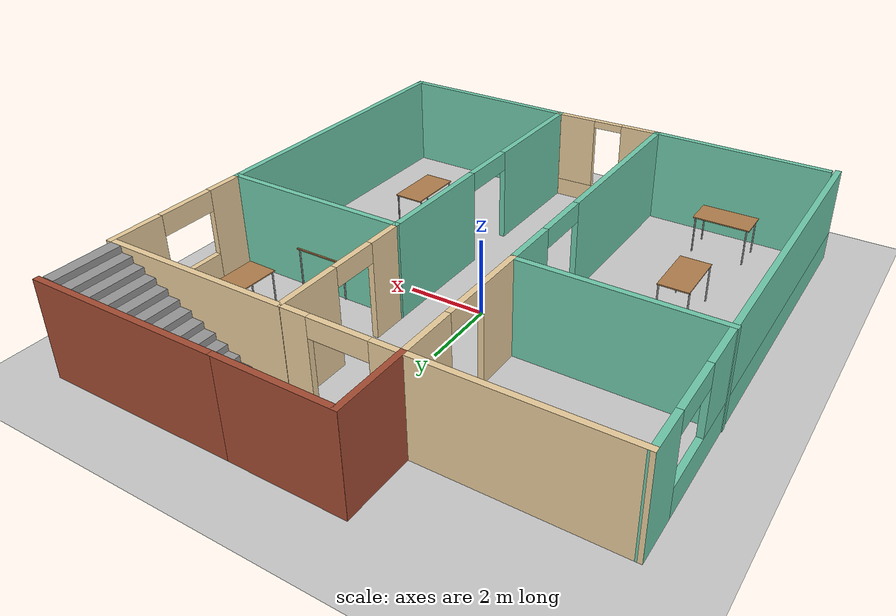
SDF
<sdf version="1.6">
 <world name="default">
  <plugin name="hello" filename="libhello.so"/>
  <light name="sun" type="directional">
   <pose>0 0 10 0 -0 0</pose>
   <diffuse>0.8 0.8 0.8 1</diffuse>
   <specular>0.2 0.2 0.2 1</specular>
   <attenuation>
    <range>1000</range>
    <constant>0.9</constant>
    <linear>0.01</linear>
    <quadratic>0.001</quadratic>
   </attenuation>
   <direction>-0.5 0.1 -0.9</direction>
  </light>
  <model name="ground_plane">
   <static>1</static>
   <link name="link">
    <collision name="collision">
     <geometry><plane><normal>0 0 1</normal><size>100 100</size></plane></geometry>
     <surface><friction><ode><mu>100</mu><mu2>50</mu2></ode></friction></surface>
    </collision>
    <visual name="visual">
     <cast_shadows>0</cast_shadows>
     <geometry><plane><normal>0 0 1</normal><size>100 100</size></plane></geometry>
     <material>
      <script><uri>file://media/materials/scripts/gazebo.material</uri><name>Gazebo/Grey</name></script>
     </material>
    </visual>
   </link>
  </model>
  <gravity>0 0 -9.8</gravity>
  <magnetic_field>6e-06 2.3e-05 -4.2e-05</magnetic_field>
  <atmosphere type="adiabatic"/>
  <physics name="default_physics" default="0" type="ode">
   <max_step_size>0.001</max_step_size>
   <real_time_factor>1</real_time_factor>
   <real_time_update_rate>1000</real_time_update_rate>
  </physics>
  <scene><ambient>0.4 0.4 0.4 1</ambient><background>0.7 0.7 0.7 1</background><shadows>1</shadows></scene>
  <spherical_coordinates>
   <surface_model>EARTH_WGS84</surface_model>
   <latitude_deg>0</latitude_deg>
   <longitude_deg>0</longitude_deg>
   <elevation>0</elevation>
   <heading_deg>0</heading_deg>
  </spherical_coordinates>
  <model name="robot">
   <link name="link_0">
    <pose>-0.18265 0.141093 0.139854 0 -0 0</pose>
    <inertial>
     <mass>1</mass>
     <inertia>
      <ixx>0.166667</ixx>
      <ixy>0</ixy>
      <ixz>0</ixz>
      <iyy>0.166667</iyy>
      <iyz>0</iyz>
      <izz>0.166667</izz>
     </inertia>
    </inertial>
    <visual name="visual">
     <geometry><box><size>0.6 0.4 0.3</size></box></geometry>
     <material>
      <lighting>1</lighting>
      <script><uri>file://media/materials/scripts/gazebo.material</uri><name>Gazebo/Grey</name></script>
      <shader type="pixel"><normal_map>__default__</normal_map></shader>
      <ambient>0.3 0.3 0.3 1</ambient>
      <diffuse>0.7 0.7 0.7 1</diffuse>
      <specular>0.01 0.01 0.01 1</specular>
      <emissive>0 0 0 1</emissive>
     </material>
    </visual>
    <collision name="collision">
     <geometry><box><size>0.6 0.4 0.3</size></box></geometry>
     <surface>
      <friction>
       <ode><mu>1</mu><mu2>1</mu2><fdir1>0 0 0</fdir1><slip1>0</slip1><slip2>0</slip2></ode>
       <torsional>
        <coefficient>1</coefficient>
        <patch_radius>0</patch_radius>
        <surface_radius>0</surface_radius>
        <use_patch_radius>1</use_patch_radius>
        <ode><slip>0</slip></ode>
       </torsional>
      </friction>
      <bounce><restitution_coefficient>0</restitution_coefficient><threshold>1e+06</threshold></bounce>
      <contact>
       <collide_without_contact>0</collide_without_contact>
       <collide_without_contact_bitmask>1</collide_without_contact_bitmask>
       <collide_bitmask>1</collide_bitmask>
       <ode>
        <soft_cfm>0</soft_cfm>
        <soft_erp>0.2</soft_erp>
        <kp>1e+13</kp>
        <kd>1</kd>
        <max_vel>0.01</max_vel>
        <min_depth>0</min_depth>
       </ode>
       <bullet>
        <split_impulse>1</split_impulse>
        <split_impulse_penetration_threshold>-0.01</split_impulse_penetration_threshold>
        <soft_cfm>0</soft_cfm>
        <soft_erp>0.2</soft_erp>
        <kp>1e+13</kp>
        <kd>1</kd>
       </bullet>
      </contact>
     </surface>
    </collision>
   </link>
   <link name="link_1">
    <pose>-0.20265 0.341093 -0.010146 1.5707 -0 0</pose>
    <inertial>
     <mass>1</mass>
     <inertia><ixx>0.145833</ixx><ixy>0</ixy><ixz>0</ixz><iyy>0.145833</iyy><iyz>0</iyz><izz>0.125</izz></inertia>
    </inertial>
    <visual name="visual">
     <geometry><cylinder><radius>0.1</radius><length>0.05</length></cylinder></geometry>
     <material>
      <lighting>1</lighting>
      <script><uri>file://media/materials/scripts/gazebo.material</uri><name>Gazebo/Grey</name></script>
      <shader type="pixel"><normal_map>__default__</normal_map></shader>
      <ambient>0.3 0.3 0.3 1</ambient>
      <diffuse>0.7 0.7 0.7 1</diffuse>
      <specular>0.01 0.01 0.01 1</specular>
      <emissive>0 0 0 1</emissive>
     </material>
    </visual>
    <collision name="collision">
     <geometry><cylinder><radius>0.1</radius><length>0.05</length></cylinder></geometry>
     <surface>
      <friction>
       <ode><mu>1</mu><mu2>1</mu2><fdir1>0 0 0</fdir1><slip1>0</slip1><slip2>0</slip2></ode>
       <torsional>
        <coefficient>1</coefficient>
        <patch_radius>0</patch_radius>
        <surface_radius>0</surface_radius>
        <use_patch_radius>1</use_patch_radius>
        <ode><slip>0</slip></ode>
       </torsional>
      </friction>
      <bounce><restitution_coefficient>0</restitution_coefficient><threshold>1e+06</threshold></bounce>
      <contact>
       <collide_without_contact>0</collide_without_contact>
       <collide_without_contact_bitmask>1</collide_without_contact_bitmask>
       <collide_bitmask>1</collide_bitmask>
       <ode>
        <soft_cfm>0</soft_cfm>
        <soft_erp>0.2</soft_erp>
        <kp>1e+13</kp>
        <kd>1</kd>
        <max_vel>0.01</max_vel>
        <min_depth>0</min_depth>
       </ode>
       <bullet>
        <split_impulse>1</split_impulse>
        <split_impulse_penetration_threshold>-0.01</split_impulse_penetration_threshold>
        <soft_cfm>0</soft_cfm>
        <soft_erp>0.2</soft_erp>
        <kp>1e+13</kp>
        <kd>1</kd>
       </bullet>
      </contact>
     </surface>
    </collision>
   </link>
   <link name="link_1_clone">
    <pose>-0.18265 -0.058907 -0.010146 1.5707 -0 0</pose>
    <inertial>
     <mass>1</mass>
     <inertia><ixx>0.145833</ixx><ixy>0</ixy><ixz>0</ixz><iyy>0.145833</iyy><iyz>0</iyz><izz>0.125</izz></inertia>
    </inertial>
    <visual name="visual">
     <geometry><cylinder><radius>0.1</radius><length>0.05</length></cylinder></geometry>
     <material>
      <lighting>1</lighting>
      <script><uri>file://media/materials/scripts/gazebo.material</uri><name>Gazebo/Grey</name></script>
      <shader type="pixel"><normal_map>__default__</normal_map></shader>
      <ambient>0.3 0.3 0.3 1</ambient>
      <diffuse>0.7 0.7 0.7 1</diffuse>
      <specular>0.01 0.01 0.01 1</specular>
      <emissive>0 0 0 1</emissive>
     </material>
    </visual>
    <collision name="collision">
     <geometry><cylinder><radius>0.1</radius><length>0.05</length></cylinder></geometry>
     <surface>
      <friction>
       <ode><mu>1</mu><mu2>1</mu2><fdir1>0 0 0</fdir1><slip1>0</slip1><slip2>0</slip2></ode>
       <torsional>
        <coefficient>1</coefficient>
        <patch_radius>0</patch_radius>
        <surface_radius>0</surface_radius>
        <use_patch_radius>1</use_patch_radius>
        <ode><slip>0</slip></ode>
       </torsional>
      </friction>
      <bounce><restitution_coefficient>0</restitution_coefficient><threshold>1e+06</threshold></bounce>
      <contact>
       <collide_without_contact>0</collide_without_contact>
       <collide_without_contact_bitmask>1</collide_without_contact_bitmask>
       <collide_bitmask>1</collide_bitmask>
       <ode>
        <soft_cfm>0</soft_cfm>
        <soft_erp>0.2</soft_erp>
        <kp>1e+13</kp>
        <kd>1</kd>
        <max_vel>0.01</max_vel>
        <min_depth>0</min_depth>
       </ode>
       <bullet>
        <split_impulse>1</split_impulse>
        <split_impulse_penetration_threshold>-0.01</split_impulse_penetration_threshold>
        <soft_cfm>0</soft_cfm>
        <soft_erp>0.2</soft_erp>
        <kp>1e+13</kp>
        <kd>1</kd>
       </bullet>
      </contact>
     </surface>
    </collision>
   </link>
   <joint name="link_0_JOINT_0" type="revolute">
    <parent>link_0</parent>
    <child>link_1_clone</child>
    <axis>
     <xyz>1 0 0</xyz>
     <use_parent_model_frame>0</use_parent_model_frame>
     <limit>
      <lower>-1.79769e+308</lower>
      <upper>1.79769e+308</upper>
      <effort>-1</effort>
      <velocity>-1</velocity>
     </limit>
     <dynamics>
      <spring_reference>0</spring_reference>
      <spring_stiffness>0</spring_stiffness>
      <damping>0</damping>
     </dynamics>
    </axis>
    <physics>
     <ode><limit><cfm>0</cfm><erp>0.2</erp></limit><suspension><cfm>0</cfm><erp>0.2</erp></suspension></ode>
    </physics>
   </joint>
   <joint name="link_0_JOINT_1" type="revolute">
    <parent>link_0</parent>
    <child>link_1</child>
    <axis>
     <xyz>1 0 0</xyz>
     <use_parent_model_frame>0</use_parent_model_frame>
     <limit>
      <lower>-1.79769e+308</lower>
      <upper>1.79769e+308</upper>
      <effort>-1</effort>
      <velocity>-1</velocity>
     </limit>
     <dynamics>
      <spring_reference>0</spring_reference>
      <spring_stiffness>0</spring_stiffness>
      <damping>0</damping>
     </dynamics>
    </axis>
    <physics>
     <ode><limit><cfm>0</cfm><erp>0.2</erp></limit><suspension><cfm>0</cfm><erp>0.2</erp></suspension></ode>
    </physics>
   </joint>
   <static>0</static>
   <pose>-0.10996 -1.35477 0.051638 -0.016449 0.317824 -0.065412</pose>
  </model>
  <model name="building">
   <pose>0.088523 -0.033971 0 0 -0 0</pose>
   <link name="Stairs_0">
    <visual name="Stairs_0_Visual_0">
     <pose>1.59394 5.92691 0.083333 0 -0 1.5708</pose>
     <geometry><box><size>1.7 0.320986 0.166667</size></box></geometry>
     <material>
      <script><uri>file://media/materials/scripts/gazebo.material</uri><name>Gazebo/Grey</name></script>
      <ambient>1 1 1 1</ambient>
     </material>
     <meta><layer>0</layer></meta>
    </visual>
    <collision name="Stairs_0_Collision_0">
     <geometry><box><size>1.7 0.320986 0.166667</size></box></geometry>
     <pose>1.59394 5.92691 0.083333 0 -0 1.5708</pose>
    </collision>
    <visual name="Stairs_0_Visual_1">
     <pose>1.91492 5.92691 0.25 0 -0 1.5708</pose>
     <geometry><box><size>1.7 0.320986 0.166667</size></box></geometry>
     <material>
      <script><uri>file://media/materials/scripts/gazebo.material</uri><name>Gazebo/Grey</name></script>
      <ambient>1 1 1 1</ambient>
     </material>
     <meta><layer>0</layer></meta>
    </visual>
    <collision name="Stairs_0_Collision_1">
     <geometry><box><size>1.7 0.320986 0.166667</size></box></geometry>
     <pose>1.91492 5.92691 0.25 0 -0 1.5708</pose>
    </collision>
    <visual name="Stairs_0_Visual_2">
     <pose>2.23591 5.92691 0.416667 0 -0 1.5708</pose>
     <geometry><box><size>1.7 0.320986 0.166667</size></box></geometry>
     <material>
      <script><uri>file://media/materials/scripts/gazebo.material</uri><name>Gazebo/Grey</name></script>
      <ambient>1 1 1 1</ambient>
     </material>
     <meta><layer>0</layer></meta>
    </visual>
    <collision name="Stairs_0_Collision_2">
     <geometry><box><size>1.7 0.320986 0.166667</size></box></geometry>
     <pose>2.23591 5.92691 0.416667 0 -0 1.5708</pose>
    </collision>
    <visual name="Stairs_0_Visual_3">
     <pose>2.55689 5.92691 0.583333 0 -0 1.5708</pose>
     <geometry><box><size>1.7 0.320986 0.166667</size></box></geometry>
     <material>
      <script><uri>file://media/materials/scripts/gazebo.material</uri><name>Gazebo/Grey</name></script>
      <ambient>1 1 1 1</ambient>
     </material>
     <meta><layer>0</layer></meta>
    </visual>
    <collision name="Stairs_0_Collision_3">
     <geometry><box><size>1.7 0.320986 0.166667</size></box></geometry>
     <pose>2.55689 5.92691 0.583333 0 -0 1.5708</pose>
    </collision>
    <visual name="Stairs_0_Visual_4">
     <pose>2.87788 5.92691 0.75 0 -0 1.5708</pose>
     <geometry><box><size>1.7 0.320986 0.166667</size></box></geometry>
     <material>
      <script><uri>file://media/materials/scripts/gazebo.material</uri><name>Gazebo/Grey</name></script>
      <ambient>1 1 1 1</ambient>
     </material>
     <meta><layer>0</layer></meta>
    </visual>
    <collision name="Stairs_0_Collision_4">
     <geometry><box><size>1.7 0.320986 0.166667</size></box></geometry>
     <pose>2.87788 5.92691 0.75 0 -0 1.5708</pose>
    </collision>
    <visual name="Stairs_0_Visual_5">
     <pose>3.19887 5.92691 0.916667 0 -0 1.5708</pose>
     <geometry><box><size>1.7 0.320986 0.166667</size></box></geometry>
     <material>
      <script><uri>file://media/materials/scripts/gazebo.material</uri><name>Gazebo/Grey</name></script>
      <ambient>1 1 1 1</ambient>
     </material>
     <meta><layer>0</layer></meta>
    </visual>
    <collision name="Stairs_0_Collision_5">
     <geometry><box><size>1.7 0.320986 0.166667</size></box></geometry>
     <pose>3.19887 5.92691 0.916667 0 -0 1.5708</pose>
    </collision>
    <visual name="Stairs_0_Visual_6">
     <pose>3.51985 5.92691 1.08333 0 -0 1.5708</pose>
     <geometry><box><size>1.7 0.320986 0.166667</size></box></geometry>
     <material>
      <script><uri>file://media/materials/scripts/gazebo.material</uri><name>Gazebo/Grey</name></script>
      <ambient>1 1 1 1</ambient>
     </material>
     <meta><layer>0</layer></meta>
    </visual>
    <collision name="Stairs_0_Collision_6">
     <geometry><box><size>1.7 0.320986 0.166667</size></box></geometry>
     <pose>3.51985 5.92691 1.08333 0 -0 1.5708</pose>
    </collision>
    <visual name="Stairs_0_Visual_7">
     <pose>3.84084 5.92691 1.25 0 -0 1.5708</pose>
     <geometry><box><size>1.7 0.320986 0.166667</size></box></geometry>
     <material>
      <script><uri>file://media/materials/scripts/gazebo.material</uri><name>Gazebo/Grey</name></script>
      <ambient>1 1 1 1</ambient>
     </material>
     <meta><layer>0</layer></meta>
    </visual>
    <collision name="Stairs_0_Collision_7">
     <geometry><box><size>1.7 0.320986 0.166667</size></box></geometry>
     <pose>3.84084 5.92691 1.25 0 -0 1.5708</pose>
    </collision>
    <visual name="Stairs_0_Visual_8">
     <pose>4.16182 5.92691 1.41667 0 -0 1.5708</pose>
     <geometry><box><size>1.7 0.320986 0.166667</size></box></geometry>
     <material>
      <script><uri>file://media/materials/scripts/gazebo.material</uri><name>Gazebo/Grey</name></script>
      <ambient>1 1 1 1</ambient>
     </material>
     <meta><layer>0</layer></meta>
    </visual>
    <collision name="Stairs_0_Collision_8">
     <geometry><box><size>1.7 0.320986 0.166667</size></box></geometry>
     <pose>4.16182 5.92691 1.41667 0 -0 1.5708</pose>
    </collision>
    <visual name="Stairs_0_Visual_9">
     <pose>4.48281 5.92691 1.58333 0 -0 1.5708</pose>
     <geometry><box><size>1.7 0.320986 0.166667</size></box></geometry>
     <material>
      <script><uri>file://media/materials/scripts/gazebo.material</uri><name>Gazebo/Grey</name></script>
      <ambient>1 1 1 1</ambient>
     </material>
     <meta><layer>0</layer></meta>
    </visual>
    <collision name="Stairs_0_Collision_9">
     <geometry><box><size>1.7 0.320986 0.166667</size></box></geometry>
     <pose>4.48281 5.92691 1.58333 0 -0 1.5708</pose>
    </collision>
    <visual name="Stairs_0_Visual_10">
     <pose>4.8038 5.92691 1.75 0 -0 1.5708</pose>
     <geometry><box><size>1.7 0.320986 0.166667</size></box></geometry>
     <material>
      <script><uri>file://media/materials/scripts/gazebo.material</uri><name>Gazebo/Grey</name></script>
      <ambient>1 1 1 1</ambient>
     </material>
     <meta><layer>0</layer></meta>
    </visual>
    <collision name="Stairs_0_Collision_10">
     <geometry><box><size>1.7 0.320986 0.166667</size></box></geometry>
     <pose>4.8038 5.92691 1.75 0 -0 1.5708</pose>
    </collision>
    <visual name="Stairs_0_Visual_11">
     <pose>5.12478 5.92691 1.91667 0 -0 1.5708</pose>
     <geometry><box><size>1.7 0.320986 0.166667</size></box></geometry>
     <material>
      <script><uri>file://media/materials/scripts/gazebo.material</uri><name>Gazebo/Grey</name></script>
      <ambient>1 1 1 1</ambient>
     </material>
     <meta><layer>0</layer></meta>
    </visual>
    <collision name="Stairs_0_Collision_11">
     <geometry><box><size>1.7 0.320986 0.166667</size></box></geometry>
     <pose>5.12478 5.92691 1.91667 0 -0 1.5708</pose>
    </collision>
    <visual name="Stairs_0_Visual_12">
     <pose>5.44577 5.92691 2.08333 0 -0 1.5708</pose>
     <geometry><box><size>1.7 0.320986 0.166667</size></box></geometry>
     <material>
      <script><uri>file://media/materials/scripts/gazebo.material</uri><name>Gazebo/Grey</name></script>
      <ambient>1 1 1 1</ambient>
     </material>
     <meta><layer>0</layer></meta>
    </visual>
    <collision name="Stairs_0_Collision_12">
     <geometry><box><size>1.7 0.320986 0.166667</size></box></geometry>
     <pose>5.44577 5.92691 2.08333 0 -0 1.5708</pose>
    </collision>
    <visual name="Stairs_0_Visual_13">
     <pose>5.76675 5.92691 2.25 0 -0 1.5708</pose>
     <geometry><box><size>1.7 0.320986 0.166667</size></box></geometry>
     <material>
      <script><uri>file://media/materials/scripts/gazebo.material</uri><name>Gazebo/Grey</name></script>
      <ambient>1 1 1 1</ambient>
     </material>
     <meta><layer>0</layer></meta>
    </visual>
    <collision name="Stairs_0_Collision_13">
     <geometry><box><size>1.7 0.320986 0.166667</size></box></geometry>
     <pose>5.76675 5.92691 2.25 0 -0 1.5708</pose>
    </collision>
    <visual name="Stairs_0_Visual_14">
     <pose>6.08774 5.92691 2.41667 0 -0 1.5708</pose>
     <geometry><box><size>1.7 0.320986 0.166667</size></box></geometry>
     <material>
      <script><uri>file://media/materials/scripts/gazebo.material</uri><name>Gazebo/Grey</name></script>
      <ambient>1 1 1 1</ambient>
     </material>
     <meta><layer>0</layer></meta>
    </visual>
    <collision name="Stairs_0_Collision_14">
     <geometry><box><size>1.7 0.320986 0.166667</size></box></geometry>
     <pose>6.08774 5.92691 2.41667 0 -0 1.5708</pose>
    </collision>
   </link>
   <link name="Wall_0">
    <collision name="Wall_0_Collision">
     <geometry><box><size>3 0.15 2.5</size></box></geometry>
     <pose>0 0 1.25 0 -0 0</pose>
    </collision>
    <visual name="Wall_0_Visual">
     <pose>0 0 1.25 0 -0 0</pose>
     <geometry><box><size>3 0.15 2.5</size></box></geometry>
     <material>
      <script><uri>file://media/materials/scripts/gazebo.material</uri><name>Gazebo/Bricks</name></script>
      <ambient>1 1 1 1</ambient>
     </material>
     <meta><layer>0</layer></meta>
    </visual>
    <pose>-0.046466 6.84416 0 0 -0 3.14159</pose>
   </link>
   <link name="Wall_1">
    <collision name="Wall_1_Collision">
     <geometry><box><size>2 0.15 2.5</size></box></geometry>
     <pose>0 0 1.25 0 -0 0</pose>
    </collision>
    <visual name="Wall_1_Visual">
     <pose>0 0 1.25 0 -0 0</pose>
     <geometry><box><size>2 0.15 2.5</size></box></geometry>
     <material>
      <script><uri>file://media/materials/scripts/gazebo.material</uri><name>Gazebo/Bricks</name></script>
      <ambient>1 1 1 1</ambient>
     </material>
     <meta><layer>0</layer></meta>
    </visual>
    <pose>-1.47147 5.91916 0 0 0 -1.5708</pose>
   </link>
   <link name="Wall_10">
    <collision name="Wall_10_Collision">
     <geometry><box><size>5 0.15 2.5</size></box></geometry>
     <pose>0 0 1.25 0 -0 0</pose>
    </collision>
    <visual name="Wall_10_Visual">
     <pose>0 0 1.25 0 -0 0</pose>
     <geometry><box><size>5 0.15 2.5</size></box></geometry>
     <material>
      <script><uri>file://media/materials/scripts/gazebo.material</uri><name>Gazebo/Grey</name></script>
      <ambient>0.435294 0.796078 0.67451 1</ambient>
     </material>
     <meta><layer>0</layer></meta>
    </visual>
    <pose>-3.90087 1.0402 0 0 -0 3.14159</pose>
   </link>
   <link name="Wall_12">
    <pose>1.47553 3.07898 0 0 -0 1.5708</pose>
    <visual name="Wall_12_Visual_0">
     <pose>-1.47098 0 1.25 0 -0 0</pose>
     <geometry><box><size>1.05804 0.15 2.5</size></box></geometry>
     <material>
      <script><uri>file://media/materials/scripts/gazebo.material</uri><name>Gazebo/Grey</name></script>
      <ambient>0.921569 0.807843 0.615686 1</ambient>
     </material>
     <meta><layer>0</layer></meta>
    </visual>
    <collision name="Wall_12_Collision_0">
     <geometry><box><size>1.05804 0.15 2.5</size></box></geometry>
     <pose>-1.47098 0 1.25 0 -0 0</pose>
    </collision>
    <visual name="Wall_12_Visual_1">
     <pose>1.12902 0 1.25 0 -0 0</pose>
     <geometry><box><size>1.74196 0.15 2.5</size></box></geometry>
     <material>
      <script><uri>file://media/materials/scripts/gazebo.material</uri><name>Gazebo/Grey</name></script>
      <ambient>0.921569 0.807843 0.615686 1</ambient>
     </material>
     <meta><layer>0</layer></meta>
    </visual>
    <collision name="Wall_12_Collision_1">
     <geometry><box><size>1.74196 0.15 2.5</size></box></geometry>
     <pose>1.12902 0 1.25 0 -0 0</pose>
    </collision>
    <visual name="Wall_12_Visual_2">
     <pose>-0.341962 0 2.25 0 -0 0</pose>
     <geometry><box><size>1.2 0.15 0.5</size></box></geometry>
     <material>
      <script><uri>file://media/materials/scripts/gazebo.material</uri><name>Gazebo/Grey</name></script>
      <ambient>0.921569 0.807843 0.615686 1</ambient>
     </material>
     <meta><layer>0</layer></meta>
    </visual>
    <collision name="Wall_12_Collision_2">
     <geometry><box><size>1.2 0.15 0.5</size></box></geometry>
     <pose>-0.341962 0 2.25 0 -0 0</pose>
    </collision>
   </link>
   <link name="Wall_15">
    <collision name="Wall_15_Collision">
     <geometry><box><size>5 0.15 2.5</size></box></geometry>
     <pose>0 0 1.25 0 -0 0</pose>
    </collision>
    <visual name="Wall_15_Visual">
     <pose>0 0 1.25 0 -0 0</pose>
     <geometry><box><size>5 0.15 2.5</size></box></geometry>
     <material>
      <script><uri>file://media/materials/scripts/gazebo.material</uri><name>Gazebo/Grey</name></script>
      <ambient>0.435294 0.796078 0.67451 1</ambient>
     </material>
     <meta><layer>0</layer></meta>
    </visual>
    <pose>3.90053 1.15398 0 0 -0 0</pose>
   </link>
   <link name="Wall_18">
    <pose>-1.47587 -2.8848 0 0 0 -1.5708</pose>
    <visual name="Wall_18_Visual_0">
     <pose>-3.2267 0 1.25 0 -0 0</pose>
     <geometry><box><size>1.54659 0.15 2.5</size></box></geometry>
     <material>
      <script><uri>file://media/materials/scripts/gazebo.material</uri><name>Gazebo/Grey</name></script>
      <ambient>0.435294 0.796078 0.67451 1</ambient>
     </material>
     <meta><layer>0</layer></meta>
    </visual>
    <collision name="Wall_18_Collision_0">
     <geometry><box><size>1.54659 0.15 2.5</size></box></geometry>
     <pose>-3.2267 0 1.25 0 -0 0</pose>
    </collision>
    <visual name="Wall_18_Visual_1">
     <pose>1.5233 0 1.25 0 -0 0</pose>
     <geometry><box><size>4.95341 0.15 2.5</size></box></geometry>
     <material>
      <script><uri>file://media/materials/scripts/gazebo.material</uri><name>Gazebo/Grey</name></script>
      <ambient>0.435294 0.796078 0.67451 1</ambient>
     </material>
     <meta><layer>0</layer></meta>
    </visual>
    <collision name="Wall_18_Collision_1">
     <geometry><box><size>4.95341 0.15 2.5</size></box></geometry>
     <pose>1.5233 0 1.25 0 -0 0</pose>
    </collision>
    <visual name="Wall_18_Visual_2">
     <pose>-1.70341 0 2.25 0 -0 0</pose>
     <geometry><box><size>1.5 0.15 0.5</size></box></geometry>
     <material>
      <script><uri>file://media/materials/scripts/gazebo.material</uri><name>Gazebo/Grey</name></script>
      <ambient>0.435294 0.796078 0.67451 1</ambient>
     </material>
     <meta><layer>0</layer></meta>
    </visual>
    <collision name="Wall_18_Collision_2">
     <geometry><box><size>1.5 0.15 0.5</size></box></geometry>
     <pose>-1.70341 0 2.25 0 -0 0</pose>
    </collision>
   </link>
   <link name="Wall_19">
    <collision name="Wall_19_Collision">
     <geometry><box><size>4.75 0.15 2.5</size></box></geometry>
     <pose>0 0 1.25 0 -0 0</pose>
    </collision>
    <visual name="Wall_19_Visual">
     <pose>0 0 1.25 0 -0 0</pose>
     <geometry><box><size>4.75 0.15 2.5</size></box></geometry>
     <material>
      <script><uri>file://media/materials/scripts/gazebo.material</uri><name>Gazebo/Grey</name></script>
      <ambient>0.435294 0.796078 0.67451 1</ambient>
     </material>
     <meta><layer>0</layer></meta>
    </visual>
    <pose>-3.77587 -6.8098 0 0 -0 3.14159</pose>
   </link>
   <link name="Wall_2">
    <collision name="Wall_2_Collision">
     <geometry><box><size>5 0.15 2.5</size></box></geometry>
     <pose>0 0 1.25 0 -0 0</pose>
    </collision>
    <visual name="Wall_2_Visual">
     <pose>0 0 1.25 0 -0 0</pose>
     <geometry><box><size>5 0.15 2.5</size></box></geometry>
     <material>
      <script><uri>file://media/materials/scripts/gazebo.material</uri><name>Gazebo/Grey</name></script>
      <ambient>0.921569 0.807843 0.615686 1</ambient>
     </material>
     <meta><layer>0</layer></meta>
    </visual>
    <pose>-3.89682 4.98839 0 0 0 -3.13921</pose>
   </link>
   <link name="Wall_21">
    <pose>1.45804 -2.77101 0 0 0 -1.57525</pose>
    <visual name="Wall_21_Visual_0">
     <pose>-2.38457 0 1.25 0 -0 0</pose>
     <geometry><box><size>3.23086 0.15 2.5</size></box></geometry>
     <material>
      <script><uri>file://media/materials/scripts/gazebo.material</uri><name>Gazebo/Grey</name></script>
      <ambient>0.435294 0.796078 0.67451 1</ambient>
     </material>
     <meta><layer>0</layer></meta>
    </visual>
    <collision name="Wall_21_Collision_0">
     <geometry><box><size>3.23086 0.15 2.5</size></box></geometry>
     <pose>-2.38457 0 1.25 0 -0 0</pose>
    </collision>
    <visual name="Wall_21_Visual_1">
     <pose>2.36543 0 1.25 0 -0 0</pose>
     <geometry><box><size>3.26914 0.15 2.5</size></box></geometry>
     <material>
      <script><uri>file://media/materials/scripts/gazebo.material</uri><name>Gazebo/Grey</name></script>
      <ambient>0.435294 0.796078 0.67451 1</ambient>
     </material>
     <meta><layer>0</layer></meta>
    </visual>
    <collision name="Wall_21_Collision_1">
     <geometry><box><size>3.26914 0.15 2.5</size></box></geometry>
     <pose>2.36543 0 1.25 0 -0 0</pose>
    </collision>
    <visual name="Wall_21_Visual_2">
     <pose>-0.019144 0 2.25 0 -0 0</pose>
     <geometry><box><size>1.5 0.15 0.5</size></box></geometry>
     <material>
      <script><uri>file://media/materials/scripts/gazebo.material</uri><name>Gazebo/Grey</name></script>
      <ambient>0.435294 0.796078 0.67451 1</ambient>
     </material>
     <meta><layer>0</layer></meta>
    </visual>
    <collision name="Wall_21_Collision_2">
     <geometry><box><size>1.5 0.15 0.5</size></box></geometry>
     <pose>-0.019144 0 2.25 0 -0 0</pose>
    </collision>
   </link>
   <link name="Wall_24">
    <collision name="Wall_24_Collision">
     <geometry><box><size>5 0.15 2.5</size></box></geometry>
     <pose>0 0 1.25 0 -0 0</pose>
    </collision>
    <visual name="Wall_24_Visual">
     <pose>0 0 1.25 0 -0 0</pose>
     <geometry><box><size>5 0.15 2.5</size></box></geometry>
     <material>
      <script><uri>file://media/materials/scripts/gazebo.material</uri><name>Gazebo/Grey</name></script>
      <ambient>0.921569 0.807843 0.615686 1</ambient>
     </material>
     <meta><layer>0</layer></meta>
    </visual>
    <pose>3.90053 5.00398 0 0 -0 3.14159</pose>
   </link>
   <link name="Wall_26">
    <pose>6.32553 3.07898 0 0 -0 1.5708</pose>
    <visual name="Wall_26_Visual_0">
     <pose>-1.4666 0 1.25 0 -0 0</pose>
     <geometry><box><size>1.0668 0.15 2.5</size></box></geometry>
     <material>
      <script><uri>file://media/materials/scripts/gazebo.material</uri><name>Gazebo/Grey</name></script>
      <ambient>0.921569 0.807843 0.615686 1</ambient>
     </material>
     <meta><layer>0</layer></meta>
    </visual>
    <collision name="Wall_26_Collision_0">
     <geometry><box><size>1.0668 0.15 2.5</size></box></geometry>
     <pose>-1.4666 0 1.25 0 -0 0</pose>
    </collision>
    <visual name="Wall_26_Visual_1">
     <pose>0.533401 0 0.375 0 -0 0</pose>
     <geometry><box><size>2.9332 0.15 0.75</size></box></geometry>
     <material>
      <script><uri>file://media/materials/scripts/gazebo.material</uri><name>Gazebo/Grey</name></script>
      <ambient>0.921569 0.807843 0.615686 1</ambient>
     </material>
     <meta><layer>0</layer></meta>
    </visual>
    <collision name="Wall_26_Collision_1">
     <geometry><box><size>2.9332 0.15 0.75</size></box></geometry>
     <pose>0.533401 0 0.375 0 -0 0</pose>
    </collision>
    <visual name="Wall_26_Visual_2">
     <pose>1.2834 0 1.625 0 -0 0</pose>
     <geometry><box><size>1.4332 0.15 1.75</size></box></geometry>
     <material>
      <script><uri>file://media/materials/scripts/gazebo.material</uri><name>Gazebo/Grey</name></script>
      <ambient>0.921569 0.807843 0.615686 1</ambient>
     </material>
     <meta><layer>0</layer></meta>
    </visual>
    <collision name="Wall_26_Collision_2">
     <geometry><box><size>1.4332 0.15 1.75</size></box></geometry>
     <pose>1.2834 0 1.625 0 -0 0</pose>
    </collision>
    <visual name="Wall_26_Visual_3">
     <pose>-0.183198 0 2.225 0 -0 0</pose>
     <geometry><box><size>1.5 0.15 0.55</size></box></geometry>
     <material>
      <script><uri>file://media/materials/scripts/gazebo.material</uri><name>Gazebo/Grey</name></script>
      <ambient>0.921569 0.807843 0.615686 1</ambient>
     </material>
     <meta><layer>0</layer></meta>
    </visual>
    <collision name="Wall_26_Collision_3">
     <geometry><box><size>1.5 0.15 0.55</size></box></geometry>
     <pose>-0.183198 0 2.225 0 -0 0</pose>
    </collision>
   </link>
   <link name="Wall_28">
    <collision name="Wall_28_Collision">
     <geometry><box><size>5 0.15 2.5</size></box></geometry>
     <pose>0 0 1.25 0 -0 0</pose>
    </collision>
    <visual name="Wall_28_Visual">
     <pose>0 0 1.25 0 -0 0</pose>
     <geometry><box><size>5 0.15 2.5</size></box></geometry>
     <material>
      <script><uri>file://media/materials/scripts/gazebo.material</uri><name>Gazebo/Grey</name></script>
      <ambient>0.435294 0.796078 0.67451 1</ambient>
     </material>
     <meta><layer>0</layer></meta>
    </visual>
    <pose>3.86555 -6.69602 0 0 -0 0</pose>
   </link>
   <link name="Wall_3">
    <pose>-6.29817 -0.942386 0 0 0 -1.56675</pose>
    <visual name="Wall_3_Visual_0">
     <pose>-5.39979 0 1.25 0 -0 0</pose>
     <geometry><box><size>1.20042 0.15 2.5</size></box></geometry>
     <material>
      <script><uri>file://media/materials/scripts/gazebo.material</uri><name>Gazebo/Grey</name></script>
      <ambient>0.435294 0.796078 0.67451 1</ambient>
     </material>
     <meta><layer>0</layer></meta>
    </visual>
    <collision name="Wall_3_Collision_0">
     <geometry><box><size>1.20042 0.15 2.5</size></box></geometry>
     <pose>-5.39979 0 1.25 0 -0 0</pose>
    </collision>
    <visual name="Wall_3_Visual_1">
     <pose>0.600208 0 0.375 0 -0 0</pose>
     <geometry><box><size>10.7996 0.15 0.75</size></box></geometry>
     <material>
      <script><uri>file://media/materials/scripts/gazebo.material</uri><name>Gazebo/Grey</name></script>
      <ambient>0.435294 0.796078 0.67451 1</ambient>
     </material>
     <meta><layer>0</layer></meta>
    </visual>
    <collision name="Wall_3_Collision_1">
     <geometry><box><size>10.7996 0.15 0.75</size></box></geometry>
     <pose>0.600208 0 0.375 0 -0 0</pose>
    </collision>
    <visual name="Wall_3_Visual_2">
     <pose>1.35021 0 1.625 0 -0 0</pose>
     <geometry><box><size>9.29959 0.15 1.75</size></box></geometry>
     <material>
      <script><uri>file://media/materials/scripts/gazebo.material</uri><name>Gazebo/Grey</name></script>
      <ambient>0.435294 0.796078 0.67451 1</ambient>
     </material>
     <meta><layer>0</layer></meta>
    </visual>
    <collision name="Wall_3_Collision_2">
     <geometry><box><size>9.29959 0.15 1.75</size></box></geometry>
     <pose>1.35021 0 1.625 0 -0 0</pose>
    </collision>
    <visual name="Wall_3_Visual_3">
     <pose>-4.04959 0 2.225 0 -0 0</pose>
     <geometry><box><size>1.5 0.15 0.55</size></box></geometry>
     <material>
      <script><uri>file://media/materials/scripts/gazebo.material</uri><name>Gazebo/Grey</name></script>
      <ambient>0.435294 0.796078 0.67451 1</ambient>
     </material>
     <meta><layer>0</layer></meta>
    </visual>
    <collision name="Wall_3_Collision_3">
     <geometry><box><size>1.5 0.15 0.55</size></box></geometry>
     <pose>-4.04959 0 2.225 0 -0 0</pose>
    </collision>
   </link>
   <link name="Wall_30">
    <collision name="Wall_30_Collision">
     <geometry><box><size>8.00008 0.15 2.5</size></box></geometry>
     <pose>0 0 1.25 0 -0 0</pose>
    </collision>
    <visual name="Wall_30_Visual">
     <pose>0 0 1.25 0 -0 0</pose>
     <geometry><box><size>8.00008 0.15 2.5</size></box></geometry>
     <material>
      <script><uri>file://media/materials/scripts/gazebo.material</uri><name>Gazebo/Grey</name></script>
      <ambient>0.435294 0.796078 0.67451 1</ambient>
     </material>
     <meta><layer>0</layer></meta>
    </visual>
    <pose>6.30804 -2.77101 0 0 0 -1.57525</pose>
   </link>
   <link name="Wall_32">
    <pose>-0.017657 -6.75291 0 0 -0 0.038996</pose>
    <visual name="Wall_32_Visual_0">
     <pose>-0.987911 0 1.25 0 -0 0</pose>
     <geometry><box><size>1.09282 0.15 2.5</size></box></geometry>
     <material>
      <script><uri>file://media/materials/scripts/gazebo.material</uri><name>Gazebo/Grey</name></script>
      <ambient>0.921569 0.807843 0.615686 1</ambient>
     </material>
     <meta><layer>0</layer></meta>
    </visual>
    <collision name="Wall_32_Collision_0">
     <geometry><box><size>1.09282 0.15 2.5</size></box></geometry>
     <pose>-0.987911 0 1.25 0 -0 0</pose>
    </collision>
    <visual name="Wall_32_Visual_1">
     <pose>0.546409 0 0.25 0 -0 0</pose>
     <geometry><box><size>1.97582 0.15 0.5</size></box></geometry>
     <material>
      <script><uri>file://media/materials/scripts/gazebo.material</uri><name>Gazebo/Grey</name></script>
      <ambient>0.921569 0.807843 0.615686 1</ambient>
     </material>
     <meta><layer>0</layer></meta>
    </visual>
    <collision name="Wall_32_Collision_1">
     <geometry><box><size>1.97582 0.15 0.5</size></box></geometry>
     <pose>0.546409 0 0.25 0 -0 0</pose>
    </collision>
    <visual name="Wall_32_Visual_2">
     <pose>0.946409 0 1.5 0 -0 0</pose>
     <geometry><box><size>1.17582 0.15 2</size></box></geometry>
     <material>
      <script><uri>file://media/materials/scripts/gazebo.material</uri><name>Gazebo/Grey</name></script>
      <ambient>0.921569 0.807843 0.615686 1</ambient>
     </material>
     <meta><layer>0</layer></meta>
    </visual>
    <collision name="Wall_32_Collision_2">
     <geometry><box><size>1.17582 0.15 2</size></box></geometry>
     <pose>0.946409 0 1.5 0 -0 0</pose>
    </collision>
    <visual name="Wall_32_Visual_3">
     <pose>-0.041502 0 2.4 0 -0 0</pose>
     <geometry><box><size>0.8 0.15 0.2</size></box></geometry>
     <material>
      <script><uri>file://media/materials/scripts/gazebo.material</uri><name>Gazebo/Grey</name></script>
      <ambient>0.921569 0.807843 0.615686 1</ambient>
     </material>
     <meta><layer>0</layer></meta>
    </visual>
    <collision name="Wall_32_Collision_3">
     <geometry><box><size>0.8 0.15 0.2</size></box></geometry>
     <pose>-0.041502 0 2.4 0 -0 0</pose>
    </collision>
   </link>
   <link name="Wall_6">
    <collision name="Wall_6_Collision">
     <geometry><box><size>5.04632 0.15 2.5</size></box></geometry>
     <pose>0 0 1.25 0 -0 0</pose>
    </collision>
    <visual name="Wall_6_Visual">
     <pose>0 0 1.25 0 -0 0</pose>
     <geometry><box><size>5.04632 0.15 2.5</size></box></geometry>
     <material>
      <script><uri>file://media/materials/scripts/gazebo.material</uri><name>Gazebo/Bricks</name></script>
      <ambient>1 1 1 1</ambient>
     </material>
     <meta><layer>0</layer></meta>
    </visual>
    <pose>3.82666 6.85572 0 0 0 -3.13687</pose>
   </link>
   <link name="Wall_8">
    <pose>-0.046466 4.99416 0 0 -0 3.14159</pose>
    <visual name="Wall_8_Visual_0">
     <pose>-1.14822 0 1.25 0 -0 0</pose>
     <geometry><box><size>0.703569 0.15 2.5</size></box></geometry>
     <material>
      <script><uri>file://media/materials/scripts/gazebo.material</uri><name>Gazebo/Grey</name></script>
      <ambient>0.921569 0.807843 0.615686 1</ambient>
     </material>
     <meta><layer>0</layer></meta>
    </visual>
    <collision name="Wall_8_Collision_0">
     <geometry><box><size>0.703569 0.15 2.5</size></box></geometry>
     <pose>-1.14822 0 1.25 0 -0 0</pose>
    </collision>
    <visual name="Wall_8_Visual_1">
     <pose>1.10178 0 1.25 0 -0 0</pose>
     <geometry><box><size>0.796431 0.15 2.5</size></box></geometry>
     <material>
      <script><uri>file://media/materials/scripts/gazebo.material</uri><name>Gazebo/Grey</name></script>
      <ambient>0.921569 0.807843 0.615686 1</ambient>
     </material>
     <meta><layer>0</layer></meta>
    </visual>
    <collision name="Wall_8_Collision_1">
     <geometry><box><size>0.796431 0.15 2.5</size></box></geometry>
     <pose>1.10178 0 1.25 0 -0 0</pose>
    </collision>
    <visual name="Wall_8_Visual_2">
     <pose>-0.046431 0 2.25 0 -0 0</pose>
     <geometry><box><size>1.5 0.15 0.5</size></box></geometry>
     <material>
      <script><uri>file://media/materials/scripts/gazebo.material</uri><name>Gazebo/Grey</name></script>
      <ambient>0.921569 0.807843 0.615686 1</ambient>
     </material>
     <meta><layer>0</layer></meta>
    </visual>
    <collision name="Wall_8_Collision_2">
     <geometry><box><size>1.5 0.15 0.5</size></box></geometry>
     <pose>-0.046431 0 2.25 0 -0 0</pose>
    </collision>
   </link>
   <link name="Wall_9">
    <pose>-1.47367 3.01718 0 0 0 -1.57191</pose>
    <visual name="Wall_9_Visual_0">
     <pose>-1.26717 0 1.25 0 -0 0</pose>
     <geometry><box><size>1.56963 0.15 2.5</size></box></geometry>
     <material>
      <script><uri>file://media/materials/scripts/gazebo.material</uri><name>Gazebo/Grey</name></script>
      <ambient>0.921569 0.807843 0.615686 1</ambient>
     </material>
     <meta><layer>0</layer></meta>
    </visual>
    <collision name="Wall_9_Collision_0">
     <geometry><box><size>1.56963 0.15 2.5</size></box></geometry>
     <pose>-1.26717 0 1.25 0 -0 0</pose>
    </collision>
    <visual name="Wall_9_Visual_1">
     <pose>1.38481 0 1.25 0 -0 0</pose>
     <geometry><box><size>1.33434 0.15 2.5</size></box></geometry>
     <material>
      <script><uri>file://media/materials/scripts/gazebo.material</uri><name>Gazebo/Grey</name></script>
      <ambient>0.921569 0.807843 0.615686 1</ambient>
     </material>
     <meta><layer>0</layer></meta>
    </visual>
    <collision name="Wall_9_Collision_1">
     <geometry><box><size>1.33434 0.15 2.5</size></box></geometry>
     <pose>1.38481 0 1.25 0 -0 0</pose>
    </collision>
    <visual name="Wall_9_Visual_2">
     <pose>0.117646 0 2.25 0 -0 0</pose>
     <geometry><box><size>1.2 0.15 0.5</size></box></geometry>
     <material>
      <script><uri>file://media/materials/scripts/gazebo.material</uri><name>Gazebo/Grey</name></script>
      <ambient>0.921569 0.807843 0.615686 1</ambient>
     </material>
     <meta><layer>0</layer></meta>
    </visual>
    <collision name="Wall_9_Collision_2">
     <geometry><box><size>1.2 0.15 0.5</size></box></geometry>
     <pose>0.117646 0 2.25 0 -0 0</pose>
    </collision>
   </link>
   <static>1</static>
  </model>
  <model name="table">
   <static>1</static>
   <link name="link">
    <collision name="surface">
     <pose>0 0 1 0 -0 0</pose>
     <geometry><box><size>1.5 0.8 0.03</size></box></geometry>
     <surface><friction><ode><mu>0.6</mu><mu2>0.6</mu2></ode></friction></surface>
    </collision>
    <visual name="visual1">
     <pose>0 0 1 0 -0 0</pose>
     <geometry><box><size>1.5 0.8 0.03</size></box></geometry>
     <material>
      <script><uri>file://media/materials/scripts/gazebo.material</uri><name>Gazebo/Wood</name></script>
     </material>
    </visual>
    <collision name="front_left_leg">
     <pose>0.68 0.38 0.5 0 -0 0</pose>
     <geometry><cylinder><radius>0.02</radius><length>1</length></cylinder></geometry>
    </collision>
    <visual name="front_left_leg">
     <pose>0.68 0.38 0.5 0 -0 0</pose>
     <geometry><cylinder><radius>0.02</radius><length>1</length></cylinder></geometry>
     <material>
      <script><uri>file://media/materials/scripts/gazebo.material</uri><name>Gazebo/Grey</name></script>
     </material>
    </visual>
    <collision name="front_right_leg">
     <pose>0.68 -0.38 0.5 0 -0 0</pose>
     <geometry><cylinder><radius>0.02</radius><length>1</length></cylinder></geometry>
    </collision>
    <visual name="front_right_leg">
     <pose>0.68 -0.38 0.5 0 -0 0</pose>
     <geometry><cylinder><radius>0.02</radius><length>1</length></cylinder></geometry>
     <material>
      <script><uri>file://media/materials/scripts/gazebo.material</uri><name>Gazebo/Grey</name></script>
     </material>
    </visual>
    <collision name="back_right_leg">
     <pose>-0.68 -0.38 0.5 0 -0 0</pose>
     <geometry><cylinder><radius>0.02</radius><length>1</length></cylinder></geometry>
    </collision>
    <visual name="back_right_leg">
     <pose>-0.68 -0.38 0.5 0 -0 0</pose>
     <geometry><cylinder><radius>0.02</radius><length>1</length></cylinder></geometry>
     <material>
      <script><uri>file://media/materials/scripts/gazebo.material</uri><name>Gazebo/Grey</name></script>
     </material>
    </visual>
    <collision name="back_left_leg">
     <pose>-0.68 0.38 0.5 0 -0 0</pose>
     <geometry><cylinder><radius>0.02</radius><length>1</length></cylinder></geometry>
    </collision>
    <visual name="back_left_leg">
     <pose>-0.68 0.38 0.5 0 -0 0</pose>
     <geometry><cylinder><radius>0.02</radius><length>1</length></cylinder></geometry>
     <material>
      <script><uri>file://media/materials/scripts/gazebo.material</uri><name>Gazebo/Grey</name></script>
     </material>
    </visual>
   </link>
   <pose>-3.97426 -2.65742 0 0 0 -1.56502</pose>
  </model>
  <model name="table_0">
   <static>1</static>
   <link name="link">
    <collision name="surface">
     <pose>0 0 1 0 -0 0</pose>
     <geometry><box><size>1.5 0.8 0.03</size></box></geometry>
     <surface><friction><ode><mu>0.6</mu><mu2>0.6</mu2></ode></friction></surface>
    </collision>
    <visual name="visual1">
     <pose>0 0 1 0 -0 0</pose>
     <geometry><box><size>1.5 0.8 0.03</size></box></geometry>
     <material>
      <script><uri>file://media/materials/scripts/gazebo.material</uri><name>Gazebo/Wood</name></script>
     </material>
    </visual>
    <collision name="front_left_leg">
     <pose>0.68 0.38 0.5 0 -0 0</pose>
     <geometry><cylinder><radius>0.02</radius><length>1</length></cylinder></geometry>
    </collision>
    <visual name="front_left_leg">
     <pose>0.68 0.38 0.5 0 -0 0</pose>
     <geometry><cylinder><radius>0.02</radius><length>1</length></cylinder></geometry>
     <material>
      <script><uri>file://media/materials/scripts/gazebo.material</uri><name>Gazebo/Grey</name></script>
     </material>
    </visual>
    <collision name="front_right_leg">
     <pose>0.68 -0.38 0.5 0 -0 0</pose>
     <geometry><cylinder><radius>0.02</radius><length>1</length></cylinder></geometry>
    </collision>
    <visual name="front_right_leg">
     <pose>0.68 -0.38 0.5 0 -0 0</pose>
     <geometry><cylinder><radius>0.02</radius><length>1</length></cylinder></geometry>
     <material>
      <script><uri>file://media/materials/scripts/gazebo.material</uri><name>Gazebo/Grey</name></script>
     </material>
    </visual>
    <collision name="back_right_leg">
     <pose>-0.68 -0.38 0.5 0 -0 0</pose>
     <geometry><cylinder><radius>0.02</radius><length>1</length></cylinder></geometry>
    </collision>
    <visual name="back_right_leg">
     <pose>-0.68 -0.38 0.5 0 -0 0</pose>
     <geometry><cylinder><radius>0.02</radius><length>1</length></cylinder></geometry>
     <material>
      <script><uri>file://media/materials/scripts/gazebo.material</uri><name>Gazebo/Grey</name></script>
     </material>
    </visual>
    <collision name="back_left_leg">
     <pose>-0.68 0.38 0.5 0 -0 0</pose>
     <geometry><cylinder><radius>0.02</radius><length>1</length></cylinder></geometry>
    </collision>
    <visual name="back_left_leg">
     <pose>-0.68 0.38 0.5 0 -0 0</pose>
     <geometry><cylinder><radius>0.02</radius><length>1</length></cylinder></geometry>
     <material>
      <script><uri>file://media/materials/scripts/gazebo.material</uri><name>Gazebo/Grey</name></script>
     </material>
    </visual>
   </link>
   <pose>3.8393 -3.17845 0 0 0 -1.57539</pose>
  </model>
  <model name="cabinet">
   <static>1</static>
   <link name="cabinet_bottom_plate">
    <inertial>
     <pose>0 0 -1 0 -0 0</pose>
     <inertia><ixx>2.05</ixx><ixy>0</ixy><ixz>0</ixz><iyy>2.05</iyy><iyz>0</iyz><izz>2.05</izz></inertia>
     <mass>25</mass>
    </inertial>
    <collision name="cabinet_bottom_plate_geom">
     <pose>0 0 0.01 0 -0 0</pose>
     <geometry><box><size>0.45 0.45 0.02</size></box></geometry>
    </collision>
    <visual name="cabinet_bottom_plate_geom_visual">
     <pose>0 0 0.01 0 -0 0</pose>
     <geometry><box><size>0.45 0.45 0.02</size></box></geometry>
     <material>
      <script><uri>file://media/materials/scripts/gazebo.material</uri><name>Gazebo/Wood</name></script>
     </material>
    </visual>
    <collision name="cabinet_bottom_plate_geom_cabinet_back_plate">
     <pose>0.235 0 0.51 0 -0 0</pose>
     <geometry><box><size>0.02 0.45 1.02</size></box></geometry>
    </collision>
    <visual name="cabinet_bottom_plate_geom_cabinet_back_plate_visual">
     <pose>0.235 0 0.51 0 -0 0</pose>
     <geometry><box><size>0.02 0.45 1.02</size></box></geometry>
     <material>
      <script><uri>file://media/materials/scripts/gazebo.material</uri><name>Gazebo/Wood</name></script>
     </material>
    </visual>
    <collision name="cabinet_bottom_plate_geom_cabinet_left_plate">
     <pose>0 0.235 0.51 0 -0 0</pose>
     <geometry><box><size>0.45 0.02 1.02</size></box></geometry>
    </collision>
    <visual name="cabinet_bottom_plate_geom_cabinet_left_plate_visual">
     <pose>0 0.235 0.51 0 -0 0</pose>
     <geometry><box><size>0.45 0.02 1.02</size></box></geometry>
     <material>
      <script><uri>file://media/materials/scripts/gazebo.material</uri><name>Gazebo/Wood</name></script>
     </material>
    </visual>
    <collision name="cabinet_bottom_plate_geom_cabinet_middle_plate">
     <pose>0 0 0.51 0 -0 0</pose>
     <geometry><box><size>0.45 0.45 0.02</size></box></geometry>
    </collision>
    <visual name="cabinet_bottom_plate_geom_cabinet_middle_plate_visual">
     <pose>0 0 0.51 0 -0 0</pose>
     <geometry><box><size>0.45 0.45 0.02</size></box></geometry>
     <material>
      <script><uri>file://media/materials/scripts/gazebo.material</uri><name>Gazebo/Wood</name></script>
     </material>
    </visual>
    <collision name="cabinet_bottom_plate_geom_cabinet_right_plate">
     <pose>0 -0.235 0.51 0 -0 0</pose>
     <geometry><box><size>0.45 0.02 1.02</size></box></geometry>
    </collision>
    <visual name="cabinet_bottom_plate_geom_cabinet_right_plate_visual">
     <pose>0 -0.235 0.51 0 -0 0</pose>
     <geometry><box><size>0.45 0.02 1.02</size></box></geometry>
     <material>
      <script><uri>file://media/materials/scripts/gazebo.material</uri><name>Gazebo/Wood</name></script>
     </material>
    </visual>
    <collision name="cabinet_bottom_plate_geom_cabinet_top_plate">
     <pose>0 0 1.01 0 -0 0</pose>
     <geometry><box><size>0.45 0.45 0.02</size></box></geometry>
    </collision>
    <visual name="cabinet_bottom_plate_geom_cabinet_top_plate_visual">
     <pose>0 0 1.01 0 -0 0</pose>
     <geometry><box><size>0.45 0.45 0.02</size></box></geometry>
     <material>
      <script><uri>file://media/materials/scripts/gazebo.material</uri><name>Gazebo/Wood</name></script>
     </material>
    </visual>
   </link>
   <pose>-5.91684 4.76497 0 0 -0 0</pose>
  </model>
  <model name="table_1">
   <static>1</static>
   <link name="link">
    <collision name="surface">
     <pose>0 0 1 0 -0 0</pose>
     <geometry><box><size>1.5 0.8 0.03</size></box></geometry>
     <surface><friction><ode><mu>0.6</mu><mu2>0.6</mu2></ode></friction></surface>
    </collision>
    <visual name="visual1">
     <pose>0 0 1 0 -0 0</pose>
     <geometry><box><size>1.5 0.8 0.03</size></box></geometry>
     <material>
      <script><uri>file://media/materials/scripts/gazebo.material</uri><name>Gazebo/Wood</name></script>
     </material>
    </visual>
    <collision name="front_left_leg">
     <pose>0.68 0.38 0.5 0 -0 0</pose>
     <geometry><cylinder><radius>0.02</radius><length>1</length></cylinder></geometry>
    </collision>
    <visual name="front_left_leg">
     <pose>0.68 0.38 0.5 0 -0 0</pose>
     <geometry><cylinder><radius>0.02</radius><length>1</length></cylinder></geometry>
     <material>
      <script><uri>file://media/materials/scripts/gazebo.material</uri><name>Gazebo/Grey</name></script>
     </material>
    </visual>
    <collision name="front_right_leg">
     <pose>0.68 -0.38 0.5 0 -0 0</pose>
     <geometry><cylinder><radius>0.02</radius><length>1</length></cylinder></geometry>
    </collision>
    <visual name="front_right_leg">
     <pose>0.68 -0.38 0.5 0 -0 0</pose>
     <geometry><cylinder><radius>0.02</radius><length>1</length></cylinder></geometry>
     <material>
      <script><uri>file://media/materials/scripts/gazebo.material</uri><name>Gazebo/Grey</name></script>
     </material>
    </visual>
    <collision name="back_right_leg">
     <pose>-0.68 -0.38 0.5 0 -0 0</pose>
     <geometry><cylinder><radius>0.02</radius><length>1</length></cylinder></geometry>
    </collision>
    <visual name="back_right_leg">
     <pose>-0.68 -0.38 0.5 0 -0 0</pose>
     <geometry><cylinder><radius>0.02</radius><length>1</length></cylinder></geometry>
     <material>
      <script><uri>file://media/materials/scripts/gazebo.material</uri><name>Gazebo/Grey</name></script>
     </material>
    </visual>
    <collision name="back_left_leg">
     <pose>-0.68 0.38 0.5 0 -0 0</pose>
     <geometry><cylinder><radius>0.02</radius><length>1</length></cylinder></geometry>
    </collision>
    <visual name="back_left_leg">
     <pose>-0.68 0.38 0.5 0 -0 0</pose>
     <geometry><cylinder><radius>0.02</radius><length>1</length></cylinder></geometry>
     <material>
      <script><uri>file://media/materials/scripts/gazebo.material</uri><name>Gazebo/Grey</name></script>
     </material>
    </visual>
   </link>
   <pose>-4.12936 3.66509 0 0 -0 0</pose>
  </model>
  <model name="table_2">
   <static>1</static>
   <link name="link">
    <collision name="surface">
     <pose>0 0 1 0 -0 0</pose>
     <geometry><box><size>1.5 0.8 0.03</size></box></geometry>
     <surface><friction><ode><mu>0.6</mu><mu2>0.6</mu2></ode></friction></surface>
    </collision>
    <visual name="visual1">
     <pose>0 0 1 0 -0 0</pose>
     <geometry><box><size>1.5 0.8 0.03</size></box></geometry>
     <material>
      <script><uri>file://media/materials/scripts/gazebo.material</uri><name>Gazebo/Wood</name></script>
     </material>
    </visual>
    <collision name="front_left_leg">
     <pose>0.68 0.38 0.5 0 -0 0</pose>
     <geometry><cylinder><radius>0.02</radius><length>1</length></cylinder></geometry>
    </collision>
    <visual name="front_left_leg">
     <pose>0.68 0.38 0.5 0 -0 0</pose>
     <geometry><cylinder><radius>0.02</radius><length>1</length></cylinder></geometry>
     <material>
      <script><uri>file://media/materials/scripts/gazebo.material</uri><name>Gazebo/Grey</name></script>
     </material>
    </visual>
    <collision name="front_right_leg">
     <pose>0.68 -0.38 0.5 0 -0 0</pose>
     <geometry><cylinder><radius>0.02</radius><length>1</length></cylinder></geometry>
    </collision>
    <visual name="front_right_leg">
     <pose>0.68 -0.38 0.5 0 -0 0</pose>
     <geometry><cylinder><radius>0.02</radius><length>1</length></cylinder></geometry>
     <material>
      <script><uri>file://media/materials/scripts/gazebo.material</uri><name>Gazebo/Grey</name></script>
     </material>
    </visual>
    <collision name="back_right_leg">
     <pose>-0.68 -0.38 0.5 0 -0 0</pose>
     <geometry><cylinder><radius>0.02</radius><length>1</length></cylinder></geometry>
    </collision>
    <visual name="back_right_leg">
     <pose>-0.68 -0.38 0.5 0 -0 0</pose>
     <geometry><cylinder><radius>0.02</radius><length>1</length></cylinder></geometry>
     <material>
      <script><uri>file://media/materials/scripts/gazebo.material</uri><name>Gazebo/Grey</name></script>
     </material>
    </visual>
    <collision name="back_left_leg">
     <pose>-0.68 0.38 0.5 0 -0 0</pose>
     <geometry><cylinder><radius>0.02</radius><length>1</length></cylinder></geometry>
    </collision>
    <visual name="back_left_leg">
     <pose>-0.68 0.38 0.5 0 -0 0</pose>
     <geometry><cylinder><radius>0.02</radius><length>1</length></cylinder></geometry>
     <material>
      <script><uri>file://media/materials/scripts/gazebo.material</uri><name>Gazebo/Grey</name></script>
     </material>
    </visual>
   </link>
   <pose>4.71806 3.06355 0.01204 0 -0 1.54897</pose>
  </model>
  <model name="cabinet_0">
   <static>1</static>
   <link name="cabinet_bottom_plate">
    <inertial>
     <pose>0 0 -1 0 -0 0</pose>
     <inertia><ixx>2.05</ixx><ixy>0</ixy><ixz>0</ixz><iyy>2.05</iyy><iyz>0</iyz><izz>2.05</izz></inertia>
     <mass>25</mass>
    </inertial>
    <collision name="cabinet_bottom_plate_geom">
     <pose>0 0 0.01 0 -0 0</pose>
     <geometry><box><size>0.45 0.45 0.02</size></box></geometry>
    </collision>
    <visual name="cabinet_bottom_plate_geom_visual">
     <pose>0 0 0.01 0 -0 0</pose>
     <geometry><box><size>0.45 0.45 0.02</size></box></geometry>
     <material>
      <script><uri>file://media/materials/scripts/gazebo.material</uri><name>Gazebo/Wood</name></script>
     </material>
    </visual>
    <collision name="cabinet_bottom_plate_geom_cabinet_back_plate">
     <pose>0.235 0 0.51 0 -0 0</pose>
     <geometry><box><size>0.02 0.45 1.02</size></box></geometry>
    </collision>
    <visual name="cabinet_bottom_plate_geom_cabinet_back_plate_visual">
     <pose>0.235 0 0.51 0 -0 0</pose>
     <geometry><box><size>0.02 0.45 1.02</size></box></geometry>
     <material>
      <script><uri>file://media/materials/scripts/gazebo.material</uri><name>Gazebo/Wood</name></script>
     </material>
    </visual>
    <collision name="cabinet_bottom_plate_geom_cabinet_left_plate">
     <pose>0 0.235 0.51 0 -0 0</pose>
     <geometry><box><size>0.45 0.02 1.02</size></box></geometry>
    </collision>
    <visual name="cabinet_bottom_plate_geom_cabinet_left_plate_visual">
     <pose>0 0.235 0.51 0 -0 0</pose>
     <geometry><box><size>0.45 0.02 1.02</size></box></geometry>
     <material>
      <script><uri>file://media/materials/scripts/gazebo.material</uri><name>Gazebo/Wood</name></script>
     </material>
    </visual>
    <collision name="cabinet_bottom_plate_geom_cabinet_middle_plate">
     <pose>0 0 0.51 0 -0 0</pose>
     <geometry><box><size>0.45 0.45 0.02</size></box></geometry>
    </collision>
    <visual name="cabinet_bottom_plate_geom_cabinet_middle_plate_visual">
     <pose>0 0 0.51 0 -0 0</pose>
     <geometry><box><size>0.45 0.45 0.02</size></box></geometry>
     <material>
      <script><uri>file://media/materials/scripts/gazebo.material</uri><name>Gazebo/Wood</name></script>
     </material>
    </visual>
    <collision name="cabinet_bottom_plate_geom_cabinet_right_plate">
     <pose>0 -0.235 0.51 0 -0 0</pose>
     <geometry><box><size>0.45 0.02 1.02</size></box></geometry>
    </collision>
    <visual name="cabinet_bottom_plate_geom_cabinet_right_plate_visual">
     <pose>0 -0.235 0.51 0 -0 0</pose>
     <geometry><box><size>0.45 0.02 1.02</size></box></geometry>
     <material>
      <script><uri>file://media/materials/scripts/gazebo.material</uri><name>Gazebo/Wood</name></script>
     </material>
    </visual>
    <collision name="cabinet_bottom_plate_geom_cabinet_top_plate">
     <pose>0 0 1.01 0 -0 0</pose>
     <geometry><box><size>0.45 0.45 0.02</size></box></geometry>
    </collision>
    <visual name="cabinet_bottom_plate_geom_cabinet_top_plate_visual">
     <pose>0 0 1.01 0 -0 0</pose>
     <geometry><box><size>0.45 0.45 0.02</size></box></geometry>
     <material>
      <script><uri>file://media/materials/scripts/gazebo.material</uri><name>Gazebo/Wood</name></script>
     </material>
    </visual>
   </link>
   <pose>5.8872 0.845437 0 0 -0 0</pose>
  </model>
  <model name="table_3">
   <static>1</static>
   <link name="link">
    <collision name="surface">
     <pose>0 0 1 0 -0 0</pose>
     <geometry><box><size>1.5 0.8 0.03</size></box></geometry>
     <surface><friction><ode><mu>0.6</mu><mu2>0.6</mu2></ode></friction></surface>
    </collision>
    <visual name="visual1">
     <pose>0 0 1 0 -0 0</pose>
     <geometry><box><size>1.5 0.8 0.03</size></box></geometry>
     <material>
      <script><uri>file://media/materials/scripts/gazebo.material</uri><name>Gazebo/Wood</name></script>
     </material>
    </visual>
    <collision name="front_left_leg">
     <pose>0.68 0.38 0.5 0 -0 0</pose>
     <geometry><cylinder><radius>0.02</radius><length>1</length></cylinder></geometry>
    </collision>
    <visual name="front_left_leg">
     <pose>0.68 0.38 0.5 0 -0 0</pose>
     <geometry><cylinder><radius>0.02</radius><length>1</length></cylinder></geometry>
     <material>
      <script><uri>file://media/materials/scripts/gazebo.material</uri><name>Gazebo/Grey</name></script>
     </material>
    </visual>
    <collision name="front_right_leg">
     <pose>0.68 -0.38 0.5 0 -0 0</pose>
     <geometry><cylinder><radius>0.02</radius><length>1</length></cylinder></geometry>
    </collision>
    <visual name="front_right_leg">
     <pose>0.68 -0.38 0.5 0 -0 0</pose>
     <geometry><cylinder><radius>0.02</radius><length>1</length></cylinder></geometry>
     <material>
      <script><uri>file://media/materials/scripts/gazebo.material</uri><name>Gazebo/Grey</name></script>
     </material>
    </visual>
    <collision name="back_right_leg">
     <pose>-0.68 -0.38 0.5 0 -0 0</pose>
     <geometry><cylinder><radius>0.02</radius><length>1</length></cylinder></geometry>
    </collision>
    <visual name="back_right_leg">
     <pose>-0.68 -0.38 0.5 0 -0 0</pose>
     <geometry><cylinder><radius>0.02</radius><length>1</length></cylinder></geometry>
     <material>
      <script><uri>file://media/materials/scripts/gazebo.material</uri><name>Gazebo/Grey</name></script>
     </material>
    </visual>
    <collision name="back_left_leg">
     <pose>-0.68 0.38 0.5 0 -0 0</pose>
     <geometry><cylinder><radius>0.02</radius><length>1</length></cylinder></geometry>
    </collision>
    <visual name="back_left_leg">
     <pose>-0.68 0.38 0.5 0 -0 0</pose>
     <geometry><cylinder><radius>0.02</radius><length>1</length></cylinder></geometry>
     <material>
      <script><uri>file://media/materials/scripts/gazebo.material</uri><name>Gazebo/Grey</name></script>
     </material>
    </visual>
   </link>
   <pose>3.8292 0.836681 0 0 -0 0</pose>
  </model>
  <model name="table_4">
   <static>1</static>
   <link name="link">
    <collision name="surface">
     <pose>0 0 1 0 -0 0</pose>
     <geometry><box><size>1.5 0.8 0.03</size></box></geometry>
     <surface><friction><ode><mu>0.6</mu><mu2>0.6</mu2></ode></friction></surface>
    </collision>
    <visual name="visual1">
     <pose>0 0 1 0 -0 0</pose>
     <geometry><box><size>1.5 0.8 0.03</size></box></geometry>
     <material>
      <script><uri>file://media/materials/scripts/gazebo.material</uri><name>Gazebo/Wood</name></script>
     </material>
    </visual>
    <collision name="front_left_leg">
     <pose>0.68 0.38 0.5 0 -0 0</pose>
     <geometry><cylinder><radius>0.02</radius><length>1</length></cylinder></geometry>
    </collision>
    <visual name="front_left_leg">
     <pose>0.68 0.38 0.5 0 -0 0</pose>
     <geometry><cylinder><radius>0.02</radius><length>1</length></cylinder></geometry>
     <material>
      <script><uri>file://media/materials/scripts/gazebo.material</uri><name>Gazebo/Grey</name></script>
     </material>
    </visual>
    <collision name="front_right_leg">
     <pose>0.68 -0.38 0.5 0 -0 0</pose>
     <geometry><cylinder><radius>0.02</radius><length>1</length></cylinder></geometry>
    </collision>
    <visual name="front_right_leg">
     <pose>0.68 -0.38 0.5 0 -0 0</pose>
     <geometry><cylinder><radius>0.02</radius><length>1</length></cylinder></geometry>
     <material>
      <script><uri>file://media/materials/scripts/gazebo.material</uri><name>Gazebo/Grey</name></script>
     </material>
    </visual>
    <collision name="back_right_leg">
     <pose>-0.68 -0.38 0.5 0 -0 0</pose>
     <geometry><cylinder><radius>0.02</radius><length>1</length></cylinder></geometry>
    </collision>
    <visual name="back_right_leg">
     <pose>-0.68 -0.38 0.5 0 -0 0</pose>
     <geometry><cylinder><radius>0.02</radius><length>1</length></cylinder></geometry>
     <material>
      <script><uri>file://media/materials/scripts/gazebo.material</uri><name>Gazebo/Grey</name></script>
     </material>
    </visual>
    <collision name="back_left_leg">
     <pose>-0.68 0.38 0.5 0 -0 0</pose>
     <geometry><cylinder><radius>0.02</radius><length>1</length></cylinder></geometry>
    </collision>
    <visual name="back_left_leg">
     <pose>-0.68 0.38 0.5 0 -0 0</pose>
     <geometry><cylinder><radius>0.02</radius><length>1</length></cylinder></geometry>
     <material>
      <script><uri>file://media/materials/scripts/gazebo.material</uri><name>Gazebo/Grey</name></script>
     </material>
    </visual>
   </link>
   <pose>-3.85573 -5.87824 0 0 -0 0</pose>
  </model>
  <model name="robot2">
   <link name="link_0">
    <pose>-0.200401 -0.001883 -0.075891 0 -0 0</pose>
    <inertial>
     <mass>1</mass>
     <inertia>
      <ixx>0.166667</ixx>
      <ixy>0</ixy>
      <ixz>0</ixz>
      <iyy>0.166667</iyy>
      <iyz>0</iyz>
      <izz>0.166667</izz>
     </inertia>
    </inertial>
    <visual name="visual">
     <geometry><box><size>0.3 0.4 0.2</size></box></geometry>
     <material>
      <lighting>1</lighting>
      <script><uri>file://media/materials/scripts/gazebo.material</uri><name>Gazebo/Grey</name></script>
      <shader type="pixel"><normal_map>__default__</normal_map></shader>
      <ambient>0.3 0.3 0.3 1</ambient>
      <diffuse>0.7 0.7 0.7 1</diffuse>
      <specular>0.01 0.01 0.01 1</specular>
      <emissive>0 0 0 1</emissive>
     </material>
    </visual>
    <collision name="collision">
     <geometry><box><size>0.3 0.4 0.2</size></box></geometry>
     <surface>
      <friction>
       <ode><mu>1</mu><mu2>1</mu2><fdir1>0 0 0</fdir1><slip1>0</slip1><slip2>0</slip2></ode>
       <torsional>
        <coefficient>1</coefficient>
        <patch_radius>0</patch_radius>
        <surface_radius>0</surface_radius>
        <use_patch_radius>1</use_patch_radius>
        <ode><slip>0</slip></ode>
       </torsional>
      </friction>
      <bounce><restitution_coefficient>0</restitution_coefficient><threshold>1e+06</threshold></bounce>
      <contact>
       <collide_without_contact>0</collide_without_contact>
       <collide_without_contact_bitmask>1</collide_without_contact_bitmask>
       <collide_bitmask>1</collide_bitmask>
       <ode>
        <soft_cfm>0</soft_cfm>
        <soft_erp>0.2</soft_erp>
        <kp>1e+13</kp>
        <kd>1</kd>
        <max_vel>0.01</max_vel>
        <min_depth>0</min_depth>
       </ode>
       <bullet>
        <split_impulse>1</split_impulse>
        <split_impulse_penetration_threshold>-0.01</split_impulse_penetration_threshold>
        <soft_cfm>0</soft_cfm>
        <soft_erp>0.2</soft_erp>
        <kp>1e+13</kp>
        <kd>1</kd>
       </bullet>
      </contact>
     </surface>
    </collision>
   </link>
   <link name="link_1">
    <pose>-0.386156 -0.18012 -0.175891 1.5707 0 1.5707</pose>
    <inertial>
     <mass>1</mass>
     <inertia><ixx>0.145833</ixx><ixy>0</ixy><ixz>0</ixz><iyy>0.145833</iyy><iyz>0</iyz><izz>0.125</izz></inertia>
    </inertial>
    <visual name="visual">
     <geometry><cylinder><radius>0.1</radius><length>0.05</length></cylinder></geometry>
     <material>
      <lighting>1</lighting>
      <script><uri>file://media/materials/scripts/gazebo.material</uri><name>Gazebo/Grey</name></script>
      <shader type="pixel"><normal_map>__default__</normal_map></shader>
      <ambient>0.3 0.3 0.3 1</ambient>
      <diffuse>0.7 0.7 0.7 1</diffuse>
      <specular>0.01 0.01 0.01 1</specular>
      <emissive>0 0 0 1</emissive>
     </material>
    </visual>
    <collision name="collision">
     <geometry><cylinder><radius>0.1</radius><length>0.05</length></cylinder></geometry>
     <surface>
      <friction>
       <ode><mu>1</mu><mu2>1</mu2><fdir1>0 0 0</fdir1><slip1>0</slip1><slip2>0</slip2></ode>
       <torsional>
        <coefficient>1</coefficient>
        <patch_radius>0</patch_radius>
        <surface_radius>0</surface_radius>
        <use_patch_radius>1</use_patch_radius>
        <ode><slip>0</slip></ode>
       </torsional>
      </friction>
      <bounce><restitution_coefficient>0</restitution_coefficient><threshold>1e+06</threshold></bounce>
      <contact>
       <collide_without_contact>0</collide_without_contact>
       <collide_without_contact_bitmask>1</collide_without_contact_bitmask>
       <collide_bitmask>1</collide_bitmask>
       <ode>
        <soft_cfm>0</soft_cfm>
        <soft_erp>0.2</soft_erp>
        <kp>1e+13</kp>
        <kd>1</kd>
        <max_vel>0.01</max_vel>
        <min_depth>0</min_depth>
       </ode>
       <bullet>
        <split_impulse>1</split_impulse>
        <split_impulse_penetration_threshold>-0.01</split_impulse_penetration_threshold>
        <soft_cfm>0</soft_cfm>
        <soft_erp>0.2</soft_erp>
        <kp>1e+13</kp>
        <kd>1</kd>
       </bullet>
      </contact>
     </surface>
    </collision>
   </link>
   <link name="link_1_clone">
    <pose>-0.006156 -0.18012 -0.175891 1.5707 0 1.5707</pose>
    <inertial>
     <mass>1</mass>
     <inertia><ixx>0.145833</ixx><ixy>0</ixy><ixz>0</ixz><iyy>0.145833</iyy><iyz>0</iyz><izz>0.125</izz></inertia>
    </inertial>
    <visual name="visual">
     <geometry><cylinder><radius>0.1</radius><length>0.05</length></cylinder></geometry>
     <material>
      <lighting>1</lighting>
      <script><uri>file://media/materials/scripts/gazebo.material</uri><name>Gazebo/Grey</name></script>
      <shader type="pixel"><normal_map>__default__</normal_map></shader>
      <ambient>0.3 0.3 0.3 1</ambient>
      <diffuse>0.7 0.7 0.7 1</diffuse>
      <specular>0.01 0.01 0.01 1</specular>
      <emissive>0 0 0 1</emissive>
     </material>
    </visual>
    <collision name="collision">
     <geometry><cylinder><radius>0.1</radius><length>0.05</length></cylinder></geometry>
     <surface>
      <friction>
       <ode><mu>1</mu><mu2>1</mu2><fdir1>0 0 0</fdir1><slip1>0</slip1><slip2>0</slip2></ode>
       <torsional>
        <coefficient>1</coefficient>
        <patch_radius>0</patch_radius>
        <surface_radius>0</surface_radius>
        <use_patch_radius>1</use_patch_radius>
        <ode><slip>0</slip></ode>
       </torsional>
      </friction>
      <bounce><restitution_coefficient>0</restitution_coefficient><threshold>1e+06</threshold></bounce>
      <contact>
       <collide_without_contact>0</collide_without_contact>
       <collide_without_contact_bitmask>1</collide_without_contact_bitmask>
       <collide_bitmask>1</collide_bitmask>
       <ode>
        <soft_cfm>0</soft_cfm>
        <soft_erp>0.2</soft_erp>
        <kp>1e+13</kp>
        <kd>1</kd>
        <max_vel>0.01</max_vel>
        <min_depth>0</min_depth>
       </ode>
       <bullet>
        <split_impulse>1</split_impulse>
        <split_impulse_penetration_threshold>-0.01</split_impulse_penetration_threshold>
        <soft_cfm>0</soft_cfm>
        <soft_erp>0.2</soft_erp>
        <kp>1e+13</kp>
        <kd>1</kd>
       </bullet>
      </contact>
     </surface>
    </collision>
   </link>
   <link name="link_1_clone_0">
    <pose>0.003844 0.17988 -0.175891 1.5707 0 1.5707</pose>
    <inertial>
     <mass>1</mass>
     <inertia><ixx>0.145833</ixx><ixy>0</ixy><ixz>0</ixz><iyy>0.145833</iyy><iyz>0</iyz><izz>0.125</izz></inertia>
    </inertial>
    <visual name="visual">
     <geometry><cylinder><radius>0.1</radius><length>0.05</length></cylinder></geometry>
     <material>
      <lighting>1</lighting>
      <script><uri>file://media/materials/scripts/gazebo.material</uri><name>Gazebo/Grey</name></script>
      <shader type="pixel"><normal_map>__default__</normal_map></shader>
      <ambient>0.3 0.3 0.3 1</ambient>
      <diffuse>0.7 0.7 0.7 1</diffuse>
      <specular>0.01 0.01 0.01 1</specular>
      <emissive>0 0 0 1</emissive>
     </material>
    </visual>
    <collision name="collision">
     <geometry><cylinder><radius>0.1</radius><length>0.05</length></cylinder></geometry>
     <surface>
      <friction>
       <ode><mu>1</mu><mu2>1</mu2><fdir1>0 0 0</fdir1><slip1>0</slip1><slip2>0</slip2></ode>
       <torsional>
        <coefficient>1</coefficient>
        <patch_radius>0</patch_radius>
        <surface_radius>0</surface_radius>
        <use_patch_radius>1</use_patch_radius>
        <ode><slip>0</slip></ode>
       </torsional>
      </friction>
      <bounce><restitution_coefficient>0</restitution_coefficient><threshold>1e+06</threshold></bounce>
      <contact>
       <collide_without_contact>0</collide_without_contact>
       <collide_without_contact_bitmask>1</collide_without_contact_bitmask>
       <collide_bitmask>1</collide_bitmask>
       <ode>
        <soft_cfm>0</soft_cfm>
        <soft_erp>0.2</soft_erp>
        <kp>1e+13</kp>
        <kd>1</kd>
        <max_vel>0.01</max_vel>
        <min_depth>0</min_depth>
       </ode>
       <bullet>
        <split_impulse>1</split_impulse>
        <split_impulse_penetration_threshold>-0.01</split_impulse_penetration_threshold>
        <soft_cfm>0</soft_cfm>
        <soft_erp>0.2</soft_erp>
        <kp>1e+13</kp>
        <kd>1</kd>
       </bullet>
      </contact>
     </surface>
    </collision>
   </link>
   <link name="link_1_clone_1">
    <pose>-0.386156 0.17988 -0.175891 1.5707 0 1.5707</pose>
    <inertial>
     <mass>1</mass>
     <inertia><ixx>0.145833</ixx><ixy>0</ixy><ixz>0</ixz><iyy>0.145833</iyy><iyz>0</iyz><izz>0.125</izz></inertia>
    </inertial>
    <visual name="visual">
     <geometry><cylinder><radius>0.1</radius><length>0.05</length></cylinder></geometry>
     <material>
      <lighting>1</lighting>
      <script><uri>file://media/materials/scripts/gazebo.material</uri><name>Gazebo/Grey</name></script>
      <shader type="pixel"><normal_map>__default__</normal_map></shader>
      <ambient>0.3 0.3 0.3 1</ambient>
      <diffuse>0.7 0.7 0.7 1</diffuse>
      <specular>0.01 0.01 0.01 1</specular>
      <emissive>0 0 0 1</emissive>
     </material>
    </visual>
    <collision name="collision">
     <geometry><cylinder><radius>0.1</radius><length>0.05</length></cylinder></geometry>
     <surface>
      <friction>
       <ode><mu>1</mu><mu2>1</mu2><fdir1>0 0 0</fdir1><slip1>0</slip1><slip2>0</slip2></ode>
       <torsional>
        <coefficient>1</coefficient>
        <patch_radius>0</patch_radius>
        <surface_radius>0</surface_radius>
        <use_patch_radius>1</use_patch_radius>
        <ode><slip>0</slip></ode>
       </torsional>
      </friction>
      <bounce><restitution_coefficient>0</restitution_coefficient><threshold>1e+06</threshold></bounce>
      <contact>
       <collide_without_contact>0</collide_without_contact>
       <collide_without_contact_bitmask>1</collide_without_contact_bitmask>
       <collide_bitmask>1</collide_bitmask>
       <ode>
        <soft_cfm>0</soft_cfm>
        <soft_erp>0.2</soft_erp>
        <kp>1e+13</kp>
        <kd>1</kd>
        <max_vel>0.01</max_vel>
        <min_depth>0</min_depth>
       </ode>
       <bullet>
        <split_impulse>1</split_impulse>
        <split_impulse_penetration_threshold>-0.01</split_impulse_penetration_threshold>
        <soft_cfm>0</soft_cfm>
        <soft_erp>0.2</soft_erp>
        <kp>1e+13</kp>
        <kd>1</kd>
       </bullet>
      </contact>
     </surface>
    </collision>
   </link>
   <joint name="link_0_JOINT_0" type="revolute">
    <parent>link_0</parent>
    <child>link_1_clone</child>
    <axis>
     <xyz>1 0 0</xyz>
     <use_parent_model_frame>0</use_parent_model_frame>
     <limit>
      <lower>-1.79769e+308</lower>
      <upper>1.79769e+308</upper>
      <effort>-1</effort>
      <velocity>-1</velocity>
     </limit>
     <dynamics>
      <spring_reference>0</spring_reference>
      <spring_stiffness>0</spring_stiffness>
      <damping>0</damping>
     </dynamics>
    </axis>
    <physics>
     <ode><limit><cfm>0</cfm><erp>0.2</erp></limit><suspension><cfm>0</cfm><erp>0.2</erp></suspension></ode>
    </physics>
   </joint>
   <joint name="link_0_JOINT_1" type="revolute">
    <parent>link_0</parent>
    <child>link_1_clone_0</child>
    <axis>
     <xyz>1 0 0</xyz>
     <use_parent_model_frame>0</use_parent_model_frame>
     <limit>
      <lower>-1.79769e+308</lower>
      <upper>1.79769e+308</upper>
      <effort>-1</effort>
      <velocity>-1</velocity>
     </limit>
     <dynamics>
      <spring_reference>0</spring_reference>
      <spring_stiffness>0</spring_stiffness>
      <damping>0</damping>
     </dynamics>
    </axis>
    <physics>
     <ode><limit><cfm>0</cfm><erp>0.2</erp></limit><suspension><cfm>0</cfm><erp>0.2</erp></suspension></ode>
    </physics>
   </joint>
   <joint name="link_0_JOINT_2" type="revolute">
    <parent>link_0</parent>
    <child>link_1</child>
    <axis>
     <xyz>1 0 0</xyz>
     <use_parent_model_frame>0</use_parent_model_frame>
     <limit>
      <lower>-1.79769e+308</lower>
      <upper>1.79769e+308</upper>
      <effort>-1</effort>
      <velocity>-1</velocity>
     </limit>
     <dynamics>
      <spring_reference>0</spring_reference>
      <spring_stiffness>0</spring_stiffness>
      <damping>0</damping>
     </dynamics>
    </axis>
    <physics>
     <ode><limit><cfm>0</cfm><erp>0.2</erp></limit><suspension><cfm>0</cfm><erp>0.2</erp></suspension></ode>
    </physics>
   </joint>
   <joint name="link_0_JOINT_3" type="revolute">
    <parent>link_0</parent>
    <child>link_1_clone_1</child>
    <axis>
     <xyz>1 0 0</xyz>
     <use_parent_model_frame>0</use_parent_model_frame>
     <limit>
      <lower>-1.79769e+308</lower>
      <upper>1.79769e+308</upper>
      <effort>-1</effort>
      <velocity>-1</velocity>
     </limit>
     <dynamics>
      <spring_reference>0</spring_reference>
      <spring_stiffness>0</spring_stiffness>
      <damping>0</damping>
     </dynamics>
    </axis>
    <physics>
     <ode><limit><cfm>0</cfm><erp>0.2</erp></limit><suspension><cfm>0</cfm><erp>0.2</erp></suspension></ode>
    </physics>
   </joint>
   <static>0</static>
   <pose>0.096353 2.09789 0.275891 0 -0 0.006353</pose>
  </model>
  <model name="my_ball">
   <link name="link_1">
    <inertial>
     <mass>1</mass>
     <inertia><ixx>0.1</ixx><ixy>0</ixy><ixz>0</ixz><iyy>0.1</iyy><iyz>0</iyz><izz>0.1</izz></inertia>
    </inertial>
    <visual name="visual">
     <geometry><sphere><radius>0.1</radius></sphere></geometry>
     <material>
      <lighting>1</lighting>
      <script><uri>file://media/materials/scripts/gazebo.material</uri><name>Gazebo/Grey</name></script>
      <shader type="pixel"><normal_map>__default__</normal_map></shader>
      <ambient>1 1 1 1</ambient>
      <diffuse>1 1 1 1</diffuse>
      <specular>1 1 1 1</specular>
      <emissive>1 1 1 1</emissive>
     </material>
    </visual>
    <collision name="collision">
     <geometry><sphere><radius>0.1</radius></sphere></geometry>
     <surface>
      <friction>
       <ode><mu>1</mu><mu2>1</mu2><fdir1>0 0 0</fdir1><slip1>0</slip1><slip2>0</slip2></ode>
       <torsional>
        <coefficient>1</coefficient>
        <patch_radius>0</patch_radius>
        <surface_radius>0</surface_radius>
        <use_patch_radius>1</use_patch_radius>
        <ode><slip>0</slip></ode>
       </torsional>
      </friction>
      <bounce><restitution_coefficient>0</restitution_coefficient><threshold>1e+06</threshold></bounce>
      <contact>
       <collide_without_contact>0</collide_without_contact>
       <collide_without_contact_bitmask>1</collide_without_contact_bitmask>
       <collide_bitmask>1</collide_bitmask>
       <ode>
        <soft_cfm>0</soft_cfm>
        <soft_erp>0.2</soft_erp>
        <kp>1e+13</kp>
        <kd>1</kd>
        <max_vel>0.01</max_vel>
        <min_depth>0</min_depth>
       </ode>
       <bullet>
        <split_impulse>1</split_impulse>
        <split_impulse_penetration_threshold>-0.01</split_impulse_penetration_threshold>
        <soft_cfm>0</soft_cfm>
        <soft_erp>0.2</soft_erp>
        <kp>1e+13</kp>
        <kd>1</kd>
       </bullet>
      </contact>
     </surface>
    </collision>
   </link>
   <static>0</static>
   <pose>-1.58578 -1.46188 0.1 0 -0 0</pose>
  </model>
  <plugin filename="/home/fpassold/workspace_project3/catkin_ws/devel/lib/libcollision_map_creator.so" name="collision_map_creator"/>
 </world>
</sdf>
